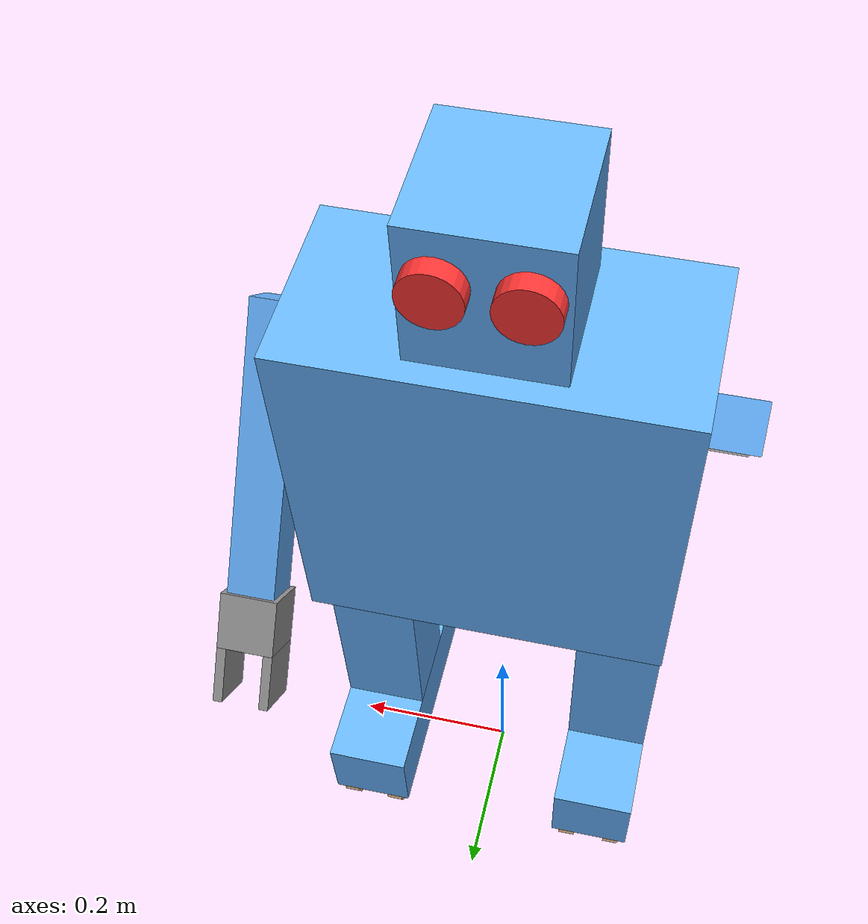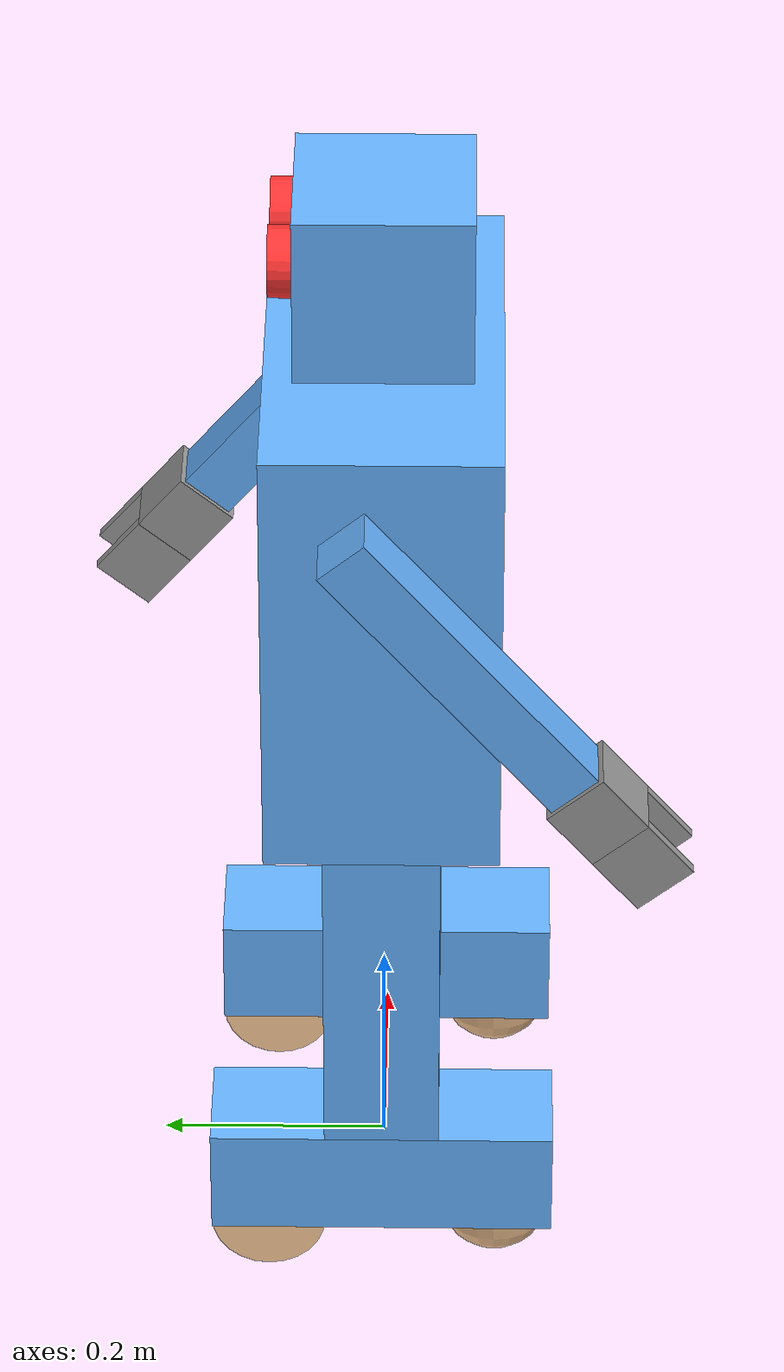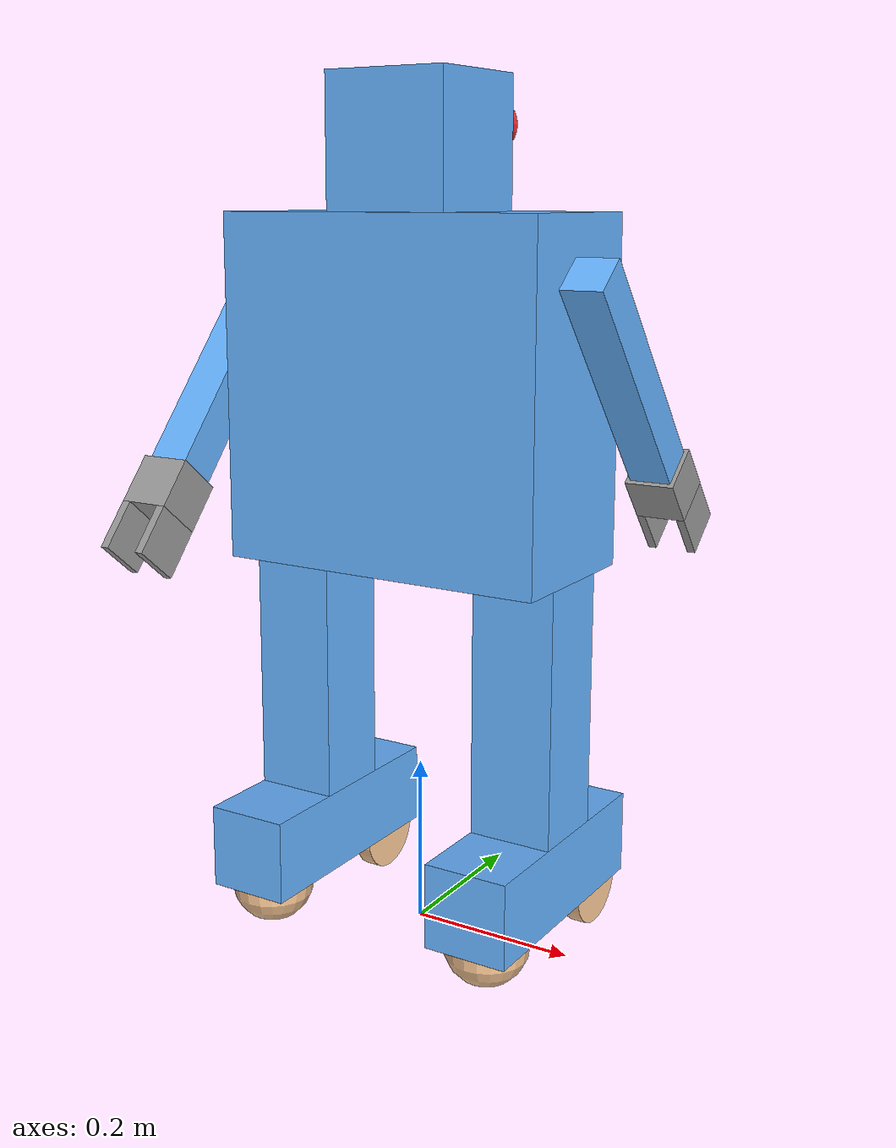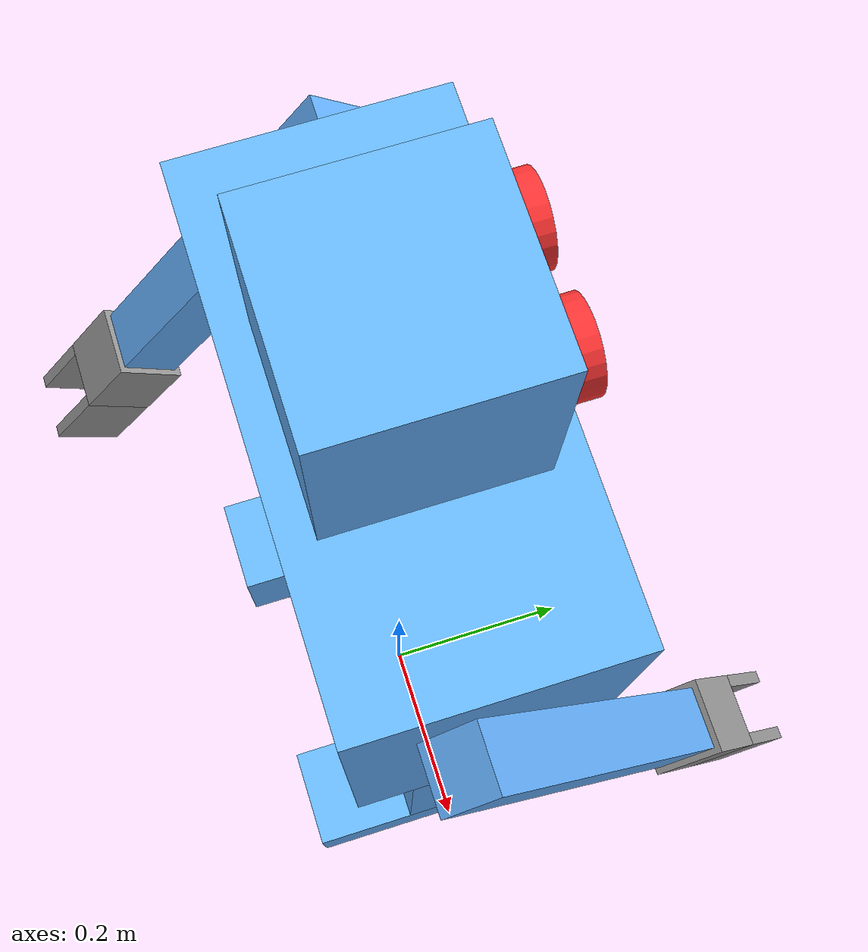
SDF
<?xml version='1.0'?>
<sdf version='1.6'>
  <model name='Vintage_Robot'>
    <link name='link_0_clone'>
      <pose frame=''>0.15 -0 0.1 0 -0 0</pose>
      <inertial>
        <mass>1</mass>
        <inertia>
          <ixx>0.166667</ixx>
          <ixy>0</ixy>
          <ixz>0</ixz>
          <iyy>0.166667</iyy>
          <iyz>0</iyz>
          <izz>0.166667</izz>
        </inertia>
        <pose frame=''>0 0 0 0 -0 0</pose>
      </inertial>
      <self_collide>0</self_collide>
      <kinematic>0</kinematic>
      <visual name='visual'>
        <pose frame=''>0 0 0 0 -0 0</pose>
        <geometry>
          <box>
            <size>0.1 0.3 0.1</size>
          </box>
        </geometry>
        <material>
          <lighting>1</lighting>
          <script>
            <uri>file://media/materials/scripts/gazebo.material</uri>
            <name>Gazebo/Grey</name>
          </script>
          <shader type='pixel'>
            <normal_map>__default__</normal_map>
          </shader>
          <ambient>0.4 0.7 1 1</ambient>
          <diffuse>0.7 0.7 0.7 1</diffuse>
          <specular>0.01 0.01 0.01 1</specular>
          <emissive>0 0 0 1</emissive>
        </material>
        <transparency>0</transparency>
        <cast_shadows>1</cast_shadows>
      </visual>
      <collision name='collision'>
        <laser_retro>0</laser_retro>
        <max_contacts>10</max_contacts>
        <pose frame=''>0 0 0 0 -0 0</pose>
        <geometry>
          <box>
            <size>0.1 0.3 0.1</size>
          </box>
        </geometry>
        <surface>
          <friction>
            <ode>
              <mu>1</mu>
              <mu2>1</mu2>
              <fdir1>0 0 0</fdir1>
              <slip1>0</slip1>
              <slip2>0</slip2>
            </ode>
            <torsional>
              <coefficient>1</coefficient>
              <patch_radius>0</patch_radius>
              <surface_radius>0</surface_radius>
              <use_patch_radius>1</use_patch_radius>
              <ode>
                <slip>0</slip>
              </ode>
            </torsional>
          </friction>
          <bounce>
            <restitution_coefficient>0</restitution_coefficient>
            <threshold>1e+06</threshold>
          </bounce>
          <contact>
            <collide_without_contact>0</collide_without_contact>
            <collide_without_contact_bitmask>1</collide_without_contact_bitmask>
            <collide_bitmask>1</collide_bitmask>
            <ode>
              <soft_cfm>0</soft_cfm>
              <soft_erp>0.2</soft_erp>
              <kp>1e+13</kp>
              <kd>1</kd>
              <max_vel>0.01</max_vel>
              <min_depth>0</min_depth>
            </ode>
            <bullet>
              <split_impulse>1</split_impulse>
              <split_impulse_penetration_threshold>-0.01</split_impulse_penetration_threshold>
              <soft_cfm>0</soft_cfm>
              <soft_erp>0.2</soft_erp>
              <kp>1e+13</kp>
              <kd>1</kd>
            </bullet>
          </contact>
        </surface>
      </collision>
    </link>
    <link name='link_0'>
      <pose frame=''>0.225 0 0.75 0.7 -0 0</pose>
      <inertial>
        <mass>1</mass>
        <inertia>
          <ixx>0.166667</ixx>
          <ixy>0</ixy>
          <ixz>0</ixz>
          <iyy>0.166667</iyy>
          <iyz>0</iyz>
          <izz>0.166667</izz>
        </inertia>
        <pose frame=''>0 0 0 0 -0 0</pose>
      </inertial>
      <self_collide>0</self_collide>
      <kinematic>0</kinematic>
      <visual name='visual'>
        <pose frame=''>0 0 -0.1 0 -0 0</pose>
        <geometry>
          <box>
            <size>0.05 0.05 0.3</size>
          </box>
        </geometry>
        <material>
          <lighting>1</lighting>
          <script>
            <uri>file://media/materials/scripts/gazebo.material</uri>
            <name>Gazebo/Grey</name>
          </script>
          <shader type='pixel'>
            <normal_map>__default__</normal_map>
          </shader>
          <ambient>0.4 0.7 1 1</ambient>
          <diffuse>0.7 0.7 0.7 1</diffuse>
          <specular>0.01 0.01 0.01 1</specular>
          <emissive>0 0 0 1</emissive>
        </material>
        <transparency>0</transparency>
        <cast_shadows>1</cast_shadows>
      </visual>
      <collision name='collision'>
        <laser_retro>0</laser_retro>
        <max_contacts>10</max_contacts>
        <pose frame=''>0 0 -0.1 0 -0 0</pose>
        <geometry>
          <box>
            <size>0.05 0.05 0.3</size>
          </box>
        </geometry>
        <surface>
          <friction>
            <ode>
              <mu>1</mu>
              <mu2>1</mu2>
              <fdir1>0 0 0</fdir1>
              <slip1>0</slip1>
              <slip2>0</slip2>
            </ode>
            <torsional>
              <coefficient>1</coefficient>
              <patch_radius>0</patch_radius>
              <surface_radius>0</surface_radius>
              <use_patch_radius>1</use_patch_radius>
              <ode>
                <slip>0</slip>
              </ode>
            </torsional>
          </friction>
          <bounce>
            <restitution_coefficient>0</restitution_coefficient>
            <threshold>1e+06</threshold>
          </bounce>
          <contact>
            <collide_without_contact>0</collide_without_contact>
            <collide_without_contact_bitmask>1</collide_without_contact_bitmask>
            <collide_bitmask>1</collide_bitmask>
            <ode>
              <soft_cfm>0</soft_cfm>
              <soft_erp>0.2</soft_erp>
              <kp>1e+13</kp>
              <kd>1</kd>
              <max_vel>0.01</max_vel>
              <min_depth>0</min_depth>
            </ode>
            <bullet>
              <split_impulse>1</split_impulse>
              <split_impulse_penetration_threshold>-0.01</split_impulse_penetration_threshold>
              <soft_cfm>0</soft_cfm>
              <soft_erp>0.2</soft_erp>
              <kp>1e+13</kp>
              <kd>1</kd>
            </bullet>
          </contact>
        </surface>
      </collision>
    </link>
    <link name='link_0_0'>
      <pose frame=''>0.04 0.08 0.945 1.5707 0 -3.14159</pose>
      <inertial>
        <mass>1</mass>
        <inertia>
          <ixx>0.145833</ixx>
          <ixy>0</ixy>
          <ixz>0</ixz>
          <iyy>0.145833</iyy>
          <iyz>0</iyz>
          <izz>0.125</izz>
        </inertia>
        <pose frame=''>0 0 0 0 -0 0</pose>
      </inertial>
      <self_collide>0</self_collide>
      <kinematic>0</kinematic>
      <visual name='visual'>
        <pose frame=''>0 0 0 0 -0 0</pose>
        <geometry>
          <cylinder>
            <radius>0.03</radius>
            <length>0.03</length>
          </cylinder>
        </geometry>
        <material>
          <lighting>1</lighting>
          <script>
            <uri>file://media/materials/scripts/gazebo.material</uri>
            <name>Gazebo/Grey</name>
          </script>
          <shader type='pixel'>
            <normal_map>__default__</normal_map>
          </shader>
          <ambient>1 0.2 0.2 1</ambient>
          <diffuse>0.7 0.7 0.7 1</diffuse>
          <specular>0.01 0.01 0.01 1</specular>
          <emissive>0 0 0 1</emissive>
        </material>
        <transparency>0</transparency>
        <cast_shadows>1</cast_shadows>
      </visual>
      <collision name='collision'>
        <laser_retro>0</laser_retro>
        <max_contacts>10</max_contacts>
        <pose frame=''>0 0 0 0 -0 0</pose>
        <geometry>
          <cylinder>
            <radius>0.03</radius>
            <length>0.03</length>
          </cylinder>
        </geometry>
        <surface>
          <friction>
            <ode>
              <mu>1</mu>
              <mu2>1</mu2>
              <fdir1>0 0 0</fdir1>
              <slip1>0</slip1>
              <slip2>0</slip2>
            </ode>
            <torsional>
              <coefficient>1</coefficient>
              <patch_radius>0</patch_radius>
              <surface_radius>0</surface_radius>
              <use_patch_radius>1</use_patch_radius>
              <ode>
                <slip>0</slip>
              </ode>
            </torsional>
          </friction>
          <bounce>
            <restitution_coefficient>0</restitution_coefficient>
            <threshold>1e+06</threshold>
          </bounce>
          <contact>
            <collide_without_contact>0</collide_without_contact>
            <collide_without_contact_bitmask>1</collide_without_contact_bitmask>
            <collide_bitmask>1</collide_bitmask>
            <ode>
              <soft_cfm>0</soft_cfm>
              <soft_erp>0.2</soft_erp>
              <kp>1e+13</kp>
              <kd>1</kd>
              <max_vel>0.01</max_vel>
              <min_depth>0</min_depth>
            </ode>
            <bullet>
              <split_impulse>1</split_impulse>
              <split_impulse_penetration_threshold>-0.01</split_impulse_penetration_threshold>
              <soft_cfm>0</soft_cfm>
              <soft_erp>0.2</soft_erp>
              <kp>1e+13</kp>
              <kd>1</kd>
            </bullet>
          </contact>
        </surface>
      </collision>
    </link>
    <link name='link_0_0_clone'>
      <pose frame=''>-0.04 0.08 0.945 1.5707 -0 5e-06</pose>
      <inertial>
        <mass>1</mass>
        <inertia>
          <ixx>0.145833</ixx>
          <ixy>0</ixy>
          <ixz>0</ixz>
          <iyy>0.145833</iyy>
          <iyz>0</iyz>
          <izz>0.125</izz>
        </inertia>
        <pose frame=''>0 0 0 0 -0 0</pose>
      </inertial>
      <self_collide>0</self_collide>
      <kinematic>0</kinematic>
      <visual name='visual_0'>
        <pose frame=''>0 0 0 0 -0 0</pose>
        <geometry>
          <cylinder>
            <radius>0.03</radius>
            <length>0.03</length>
          </cylinder>
        </geometry>
        <material>
          <lighting>1</lighting>
          <script>
            <uri>file://media/materials/scripts/gazebo.material</uri>
            <name>Gazebo/Grey</name>
          </script>
          <shader type='pixel'>
            <normal_map>__default__</normal_map>
          </shader>
          <ambient>1 0.2 0.2 1</ambient>
          <diffuse>0.7 0.7 0.7 1</diffuse>
          <specular>0.01 0.01 0.01 1</specular>
          <emissive>0 0 0 1</emissive>
        </material>
        <transparency>0</transparency>
        <cast_shadows>1</cast_shadows>
      </visual>
      <collision name='collision'>
        <laser_retro>0</laser_retro>
        <max_contacts>10</max_contacts>
        <pose frame=''>0 0 0 0 -0 0</pose>
        <geometry>
          <cylinder>
            <radius>0.03</radius>
            <length>0.03</length>
          </cylinder>
        </geometry>
        <surface>
          <friction>
            <ode>
              <mu>1</mu>
              <mu2>1</mu2>
              <fdir1>0 0 0</fdir1>
              <slip1>0</slip1>
              <slip2>0</slip2>
            </ode>
            <torsional>
              <coefficient>1</coefficient>
              <patch_radius>0</patch_radius>
              <surface_radius>0</surface_radius>
              <use_patch_radius>1</use_patch_radius>
              <ode>
                <slip>0</slip>
              </ode>
            </torsional>
          </friction>
          <bounce>
            <restitution_coefficient>0</restitution_coefficient>
            <threshold>1e+06</threshold>
          </bounce>
          <contact>
            <collide_without_contact>0</collide_without_contact>
            <collide_without_contact_bitmask>1</collide_without_contact_bitmask>
            <collide_bitmask>1</collide_bitmask>
            <ode>
              <soft_cfm>0</soft_cfm>
              <soft_erp>0.2</soft_erp>
              <kp>1e+13</kp>
              <kd>1</kd>
              <max_vel>0.01</max_vel>
              <min_depth>0</min_depth>
            </ode>
            <bullet>
              <split_impulse>1</split_impulse>
              <split_impulse_penetration_threshold>-0.01</split_impulse_penetration_threshold>
              <soft_cfm>0</soft_cfm>
              <soft_erp>0.2</soft_erp>
              <kp>1e+13</kp>
              <kd>1</kd>
            </bullet>
          </contact>
        </surface>
      </collision>
    </link>
    <link name='link_0_1'>
      <pose frame=''>-0 0 0.925 0 -0 0</pose>
      <inertial>
        <mass>1</mass>
        <inertia>
          <ixx>0.166667</ixx>
          <ixy>0</ixy>
          <ixz>0</ixz>
          <iyy>0.166667</iyy>
          <iyz>0</iyz>
          <izz>0.166667</izz>
        </inertia>
        <pose frame=''>0 0 0 0 -0 0</pose>
      </inertial>
      <self_collide>0</self_collide>
      <kinematic>0</kinematic>
      <visual name='visual'>
        <pose frame=''>0 0 0 0 -0 0</pose>
        <geometry>
          <box>
            <size>0.15 0.15 0.15</size>
          </box>
        </geometry>
        <material>
          <lighting>1</lighting>
          <script>
            <uri>file://media/materials/scripts/gazebo.material</uri>
            <name>Gazebo/Grey</name>
          </script>
          <shader type='pixel'>
            <normal_map>__default__</normal_map>
          </shader>
          <ambient>0.4 0.7 1 1</ambient>
          <diffuse>0.7 0.7 0.7 1</diffuse>
          <specular>0.01 0.01 0.01 1</specular>
          <emissive>0 0 0 1</emissive>
        </material>
        <transparency>0</transparency>
        <cast_shadows>1</cast_shadows>
      </visual>
      <collision name='collision'>
        <laser_retro>0</laser_retro>
        <max_contacts>10</max_contacts>
        <pose frame=''>0 0 0 0 -0 0</pose>
        <geometry>
          <box>
            <size>0.15 0.15 0.15</size>
          </box>
        </geometry>
        <surface>
          <friction>
            <ode>
              <mu>1</mu>
              <mu2>1</mu2>
              <fdir1>0 0 0</fdir1>
              <slip1>0</slip1>
              <slip2>0</slip2>
            </ode>
            <torsional>
              <coefficient>1</coefficient>
              <patch_radius>0</patch_radius>
              <surface_radius>0</surface_radius>
              <use_patch_radius>1</use_patch_radius>
              <ode>
                <slip>0</slip>
              </ode>
            </torsional>
          </friction>
          <bounce>
            <restitution_coefficient>0</restitution_coefficient>
            <threshold>1e+06</threshold>
          </bounce>
          <contact>
            <collide_without_contact>0</collide_without_contact>
            <collide_without_contact_bitmask>1</collide_without_contact_bitmask>
            <collide_bitmask>1</collide_bitmask>
            <ode>
              <soft_cfm>0</soft_cfm>
              <soft_erp>0.2</soft_erp>
              <kp>1e+13</kp>
              <kd>1</kd>
              <max_vel>0.01</max_vel>
              <min_depth>0</min_depth>
            </ode>
            <bullet>
              <split_impulse>1</split_impulse>
              <split_impulse_penetration_threshold>-0.01</split_impulse_penetration_threshold>
              <soft_cfm>0</soft_cfm>
              <soft_erp>0.2</soft_erp>
              <kp>1e+13</kp>
              <kd>1</kd>
            </bullet>
          </contact>
        </surface>
      </collision>
    </link>
    <link name='link_0_clone_0'>
      <pose frame=''>-0.15 -0 0.1 0 -0 0</pose>
      <inertial>
        <mass>1</mass>
        <inertia>
          <ixx>0.166667</ixx>
          <ixy>0</ixy>
          <ixz>0</ixz>
          <iyy>0.166667</iyy>
          <iyz>0</iyz>
          <izz>0.166667</izz>
        </inertia>
        <pose frame=''>0 0 0 0 -0 0</pose>
      </inertial>
      <self_collide>0</self_collide>
      <kinematic>0</kinematic>
      <visual name='visual'>
        <pose frame=''>0 0 0 0 -0 0</pose>
        <geometry>
          <box>
            <size>0.1 0.3 0.1</size>
          </box>
        </geometry>
        <material>
          <lighting>1</lighting>
          <script>
            <uri>file://media/materials/scripts/gazebo.material</uri>
            <name>Gazebo/Grey</name>
          </script>
          <shader type='pixel'>
            <normal_map>__default__</normal_map>
          </shader>
          <ambient>0.4 0.7 1 1</ambient>
          <diffuse>0.7 0.7 0.7 1</diffuse>
          <specular>0.01 0.01 0.01 1</specular>
          <emissive>0 0 0 1</emissive>
        </material>
        <transparency>0</transparency>
        <cast_shadows>1</cast_shadows>
      </visual>
      <collision name='collision'>
        <laser_retro>0</laser_retro>
        <max_contacts>10</max_contacts>
        <pose frame=''>0 0 0 0 -0 0</pose>
        <geometry>
          <box>
            <size>0.1 0.3 0.1</size>
          </box>
        </geometry>
        <surface>
          <friction>
            <ode>
              <mu>1</mu>
              <mu2>1</mu2>
              <fdir1>0 0 0</fdir1>
              <slip1>0</slip1>
              <slip2>0</slip2>
            </ode>
            <torsional>
              <coefficient>1</coefficient>
              <patch_radius>0</patch_radius>
              <surface_radius>0</surface_radius>
              <use_patch_radius>1</use_patch_radius>
              <ode>
                <slip>0</slip>
              </ode>
            </torsional>
          </friction>
          <bounce>
            <restitution_coefficient>0</restitution_coefficient>
            <threshold>1e+06</threshold>
          </bounce>
          <contact>
            <collide_without_contact>0</collide_without_contact>
            <collide_without_contact_bitmask>1</collide_without_contact_bitmask>
            <collide_bitmask>1</collide_bitmask>
            <ode>
              <soft_cfm>0</soft_cfm>
              <soft_erp>0.2</soft_erp>
              <kp>1e+13</kp>
              <kd>1</kd>
              <max_vel>0.01</max_vel>
              <min_depth>0</min_depth>
            </ode>
            <bullet>
              <split_impulse>1</split_impulse>
              <split_impulse_penetration_threshold>-0.01</split_impulse_penetration_threshold>
              <soft_cfm>0</soft_cfm>
              <soft_erp>0.2</soft_erp>
              <kp>1e+13</kp>
              <kd>1</kd>
            </bullet>
          </contact>
        </surface>
      </collision>
    </link>
    <link name='link_0_clone_1'>
      <pose frame=''>-0.225 0 0.75 -0.7 -0 -0</pose>
      <inertial>
        <mass>1</mass>
        <inertia>
          <ixx>0.166667</ixx>
          <ixy>0</ixy>
          <ixz>0</ixz>
          <iyy>0.166667</iyy>
          <iyz>0</iyz>
          <izz>0.166667</izz>
        </inertia>
        <pose frame=''>0 0 0 0 -0 0</pose>
      </inertial>
      <self_collide>0</self_collide>
      <kinematic>0</kinematic>
      <visual name='visual'>
        <pose frame=''>0 0 -0.1 0 -0 0</pose>
        <geometry>
          <box>
            <size>0.05 0.05 0.3</size>
          </box>
        </geometry>
        <material>
          <lighting>1</lighting>
          <script>
            <uri>file://media/materials/scripts/gazebo.material</uri>
            <name>Gazebo/Grey</name>
          </script>
          <shader type='pixel'>
            <normal_map>__default__</normal_map>
          </shader>
          <ambient>0.4 0.7 1 1</ambient>
          <diffuse>0.7 0.7 0.7 1</diffuse>
          <specular>0.01 0.01 0.01 1</specular>
          <emissive>0 0 0 1</emissive>
        </material>
        <transparency>0</transparency>
        <cast_shadows>1</cast_shadows>
      </visual>
      <collision name='collision'>
        <laser_retro>0</laser_retro>
        <max_contacts>10</max_contacts>
        <pose frame=''>0 0 -0.1 0 -0 0</pose>
        <geometry>
          <box>
            <size>0.05 0.05 0.3</size>
          </box>
        </geometry>
        <surface>
          <friction>
            <ode>
              <mu>1</mu>
              <mu2>1</mu2>
              <fdir1>0 0 0</fdir1>
              <slip1>0</slip1>
              <slip2>0</slip2>
            </ode>
            <torsional>
              <coefficient>1</coefficient>
              <patch_radius>0</patch_radius>
              <surface_radius>0</surface_radius>
              <use_patch_radius>1</use_patch_radius>
              <ode>
                <slip>0</slip>
              </ode>
            </torsional>
          </friction>
          <bounce>
            <restitution_coefficient>0</restitution_coefficient>
            <threshold>1e+06</threshold>
          </bounce>
          <contact>
            <collide_without_contact>0</collide_without_contact>
            <collide_without_contact_bitmask>1</collide_without_contact_bitmask>
            <collide_bitmask>1</collide_bitmask>
            <ode>
              <soft_cfm>0</soft_cfm>
              <soft_erp>0.2</soft_erp>
              <kp>1e+13</kp>
              <kd>1</kd>
              <max_vel>0.01</max_vel>
              <min_depth>0</min_depth>
            </ode>
            <bullet>
              <split_impulse>1</split_impulse>
              <split_impulse_penetration_threshold>-0.01</split_impulse_penetration_threshold>
              <soft_cfm>0</soft_cfm>
              <soft_erp>0.2</soft_erp>
              <kp>1e+13</kp>
              <kd>1</kd>
            </bullet>
          </contact>
        </surface>
      </collision>
    </link>
    <link name='link_1'>
      <pose frame=''>0.25 0.219034 0.489954 0.7 -0 0</pose>
      <inertial>
        <mass>1</mass>
        <inertia>
          <ixx>0.166667</ixx>
          <ixy>0</ixy>
          <ixz>0</ixz>
          <iyy>0.166667</iyy>
          <iyz>0</iyz>
          <izz>0.166667</izz>
        </inertia>
        <pose frame=''>0 0 0 0 -0 0</pose>
      </inertial>
      <self_collide>0</self_collide>
      <kinematic>0</kinematic>
      <visual name='visual'>
        <pose frame=''>0 0 0 0 -0 0</pose>
        <geometry>
          <box>
            <size>0.01 0.06 0.06</size>
          </box>
        </geometry>
        <material>
          <lighting>1</lighting>
          <script>
            <uri>file://media/materials/scripts/gazebo.material</uri>
            <name>Gazebo/Grey</name>
          </script>
          <shader type='pixel'>
            <normal_map>__default__</normal_map>
          </shader>
          <ambient>0.75 0.75 0.75 1</ambient>
          <diffuse>0.7 0.7 0.7 1</diffuse>
          <specular>0.01 0.01 0.01 1</specular>
          <emissive>0 0 0 1</emissive>
        </material>
        <transparency>0</transparency>
        <cast_shadows>1</cast_shadows>
      </visual>
      <collision name='collision'>
        <laser_retro>0</laser_retro>
        <max_contacts>10</max_contacts>
        <pose frame=''>0 0 0 0 -0 0</pose>
        <geometry>
          <box>
            <size>0.01 0.06 0.06</size>
          </box>
        </geometry>
        <surface>
          <friction>
            <ode>
              <mu>1</mu>
              <mu2>1</mu2>
              <fdir1>0 0 0</fdir1>
              <slip1>0</slip1>
              <slip2>0</slip2>
            </ode>
            <torsional>
              <coefficient>1</coefficient>
              <patch_radius>0</patch_radius>
              <surface_radius>0</surface_radius>
              <use_patch_radius>1</use_patch_radius>
              <ode>
                <slip>0</slip>
              </ode>
            </torsional>
          </friction>
          <bounce>
            <restitution_coefficient>0</restitution_coefficient>
            <threshold>1e+06</threshold>
          </bounce>
          <contact>
            <collide_without_contact>0</collide_without_contact>
            <collide_without_contact_bitmask>1</collide_without_contact_bitmask>
            <collide_bitmask>1</collide_bitmask>
            <ode>
              <soft_cfm>0</soft_cfm>
              <soft_erp>0.2</soft_erp>
              <kp>1e+13</kp>
              <kd>1</kd>
              <max_vel>0.01</max_vel>
              <min_depth>0</min_depth>
            </ode>
            <bullet>
              <split_impulse>1</split_impulse>
              <split_impulse_penetration_threshold>-0.01</split_impulse_penetration_threshold>
              <soft_cfm>0</soft_cfm>
              <soft_erp>0.2</soft_erp>
              <kp>1e+13</kp>
              <kd>1</kd>
            </bullet>
          </contact>
        </surface>
      </collision>
    </link>
    <link name='link_1_clone'>
      <pose frame=''>0.120005 0.1 0.05 0.001508 1.5707 0.001508</pose>
      <inertial>
        <mass>1</mass>
        <inertia>
          <ixx>0.145833</ixx>
          <ixy>0</ixy>
          <ixz>0</ixz>
          <iyy>0.145833</iyy>
          <iyz>0</iyz>
          <izz>0.125</izz>
        </inertia>
        <pose frame=''>0 0 0 0 -0 0</pose>
      </inertial>
      <self_collide>0</self_collide>
      <kinematic>0</kinematic>
      <visual name='visual'>
        <pose frame=''>0 0 0 0 -0 0</pose>
        <geometry>
          <cylinder>
            <radius>0.05</radius>
            <length>0.02</length>
          </cylinder>
        </geometry>
        <material>
          <lighting>1</lighting>
          <script>
            <uri>file://media/materials/scripts/gazebo.material</uri>
            <name>Gazebo/Grey</name>
          </script>
          <shader type='pixel'>
            <normal_map>__default__</normal_map>
          </shader>
          <ambient>1 0.8 0.6 1</ambient>
          <diffuse>0.7 0.7 0.7 1</diffuse>
          <specular>0.01 0.01 0.01 1</specular>
          <emissive>0 0 0 1</emissive>
        </material>
        <transparency>0</transparency>
        <cast_shadows>1</cast_shadows>
      </visual>
      <collision name='collision'>
        <laser_retro>0</laser_retro>
        <max_contacts>10</max_contacts>
        <pose frame=''>0 0 0 0 -0 0</pose>
        <geometry>
          <cylinder>
            <radius>0.05</radius>
            <length>0.02</length>
          </cylinder>
        </geometry>
        <surface>
          <friction>
            <ode>
              <mu>1</mu>
              <mu2>1</mu2>
              <fdir1>0 0 0</fdir1>
              <slip1>0</slip1>
              <slip2>0</slip2>
            </ode>
            <torsional>
              <coefficient>1</coefficient>
              <patch_radius>0</patch_radius>
              <surface_radius>0</surface_radius>
              <use_patch_radius>1</use_patch_radius>
              <ode>
                <slip>0</slip>
              </ode>
            </torsional>
          </friction>
          <bounce>
            <restitution_coefficient>0</restitution_coefficient>
            <threshold>1e+06</threshold>
          </bounce>
          <contact>
            <collide_without_contact>0</collide_without_contact>
            <collide_without_contact_bitmask>1</collide_without_contact_bitmask>
            <collide_bitmask>1</collide_bitmask>
            <ode>
              <soft_cfm>0</soft_cfm>
              <soft_erp>0.2</soft_erp>
              <kp>1e+13</kp>
              <kd>1</kd>
              <max_vel>0.01</max_vel>
              <min_depth>0</min_depth>
            </ode>
            <bullet>
              <split_impulse>1</split_impulse>
              <split_impulse_penetration_threshold>-0.01</split_impulse_penetration_threshold>
              <soft_cfm>0</soft_cfm>
              <soft_erp>0.2</soft_erp>
              <kp>1e+13</kp>
              <kd>1</kd>
            </bullet>
          </contact>
        </surface>
      </collision>
    </link>
    <link name='link_1_clone_0'>
      <pose frame=''>-0.179995 0.1 0.05 0.000879 1.5707 0.000879</pose>
      <inertial>
        <mass>1</mass>
        <inertia>
          <ixx>0.145833</ixx>
          <ixy>0</ixy>
          <ixz>0</ixz>
          <iyy>0.145833</iyy>
          <iyz>0</iyz>
          <izz>0.125</izz>
        </inertia>
        <pose frame=''>0 0 0 0 -0 0</pose>
      </inertial>
      <self_collide>0</self_collide>
      <kinematic>0</kinematic>
      <gravity>1</gravity>
      <visual name='visual'>
        <pose frame=''>0 0 0 0 -0 0</pose>
        <geometry>
          <cylinder>
            <radius>0.05</radius>
            <length>0.02</length>
          </cylinder>
        </geometry>
        <material>
          <lighting>1</lighting>
          <script>
            <uri>file://media/materials/scripts/gazebo.material</uri>
            <name>Gazebo/Grey</name>
          </script>
          <shader type='pixel'>
            <normal_map>__default__</normal_map>
          </shader>
          <ambient>1 0.8 0.6 1</ambient>
          <diffuse>0.7 0.7 0.7 1</diffuse>
          <specular>0.01 0.01 0.01 1</specular>
          <emissive>0 0 0 1</emissive>
        </material>
        <transparency>0</transparency>
        <cast_shadows>1</cast_shadows>
      </visual>
      <collision name='collision'>
        <laser_retro>0</laser_retro>
        <max_contacts>10</max_contacts>
        <pose frame=''>0 0 0 0 -0 0</pose>
        <geometry>
          <cylinder>
            <radius>0.05</radius>
            <length>0.02</length>
          </cylinder>
        </geometry>
        <surface>
          <friction>
            <ode>
              <mu>1</mu>
              <mu2>1</mu2>
              <fdir1>0 0 0</fdir1>
              <slip1>0</slip1>
              <slip2>0</slip2>
            </ode>
            <torsional>
              <coefficient>1</coefficient>
              <patch_radius>0</patch_radius>
              <surface_radius>0</surface_radius>
              <use_patch_radius>1</use_patch_radius>
              <ode>
                <slip>0</slip>
              </ode>
            </torsional>
          </friction>
          <bounce>
            <restitution_coefficient>0</restitution_coefficient>
            <threshold>1e+06</threshold>
          </bounce>
          <contact>
            <collide_without_contact>0</collide_without_contact>
            <collide_without_contact_bitmask>1</collide_without_contact_bitmask>
            <collide_bitmask>1</collide_bitmask>
            <ode>
              <soft_cfm>0</soft_cfm>
              <soft_erp>0.2</soft_erp>
              <kp>1e+13</kp>
              <kd>1</kd>
              <max_vel>0.01</max_vel>
              <min_depth>0</min_depth>
            </ode>
            <bullet>
              <split_impulse>1</split_impulse>
              <split_impulse_penetration_threshold>-0.01</split_impulse_penetration_threshold>
              <soft_cfm>0</soft_cfm>
              <soft_erp>0.2</soft_erp>
              <kp>1e+13</kp>
              <kd>1</kd>
            </bullet>
          </contact>
        </surface>
      </collision>
    </link>
    <link name='link_1_clone_0_clone'>
      <pose frame=''>-0.120005 0.1 0.05 0.000879 1.5707 0.000879</pose>
      <inertial>
        <mass>1</mass>
        <inertia>
          <ixx>0.145833</ixx>
          <ixy>0</ixy>
          <ixz>0</ixz>
          <iyy>0.145833</iyy>
          <iyz>0</iyz>
          <izz>0.125</izz>
        </inertia>
        <pose frame=''>0 0 0 0 -0 0</pose>
      </inertial>
      <self_collide>0</self_collide>
      <kinematic>0</kinematic>
      <visual name='visual'>
        <pose frame=''>0 0 0 0 -0 0</pose>
        <geometry>
          <cylinder>
            <radius>0.05</radius>
            <length>0.02</length>
          </cylinder>
        </geometry>
        <material>
          <lighting>1</lighting>
          <script>
            <uri>file://media/materials/scripts/gazebo.material</uri>
            <name>Gazebo/Grey</name>
          </script>
          <shader type='pixel'>
            <normal_map>__default__</normal_map>
          </shader>
          <ambient>1 0.8 0.6 1</ambient>
          <diffuse>0.7 0.7 0.7 1</diffuse>
          <specular>0.01 0.01 0.01 1</specular>
          <emissive>0 0 0 1</emissive>
        </material>
        <transparency>0</transparency>
        <cast_shadows>1</cast_shadows>
      </visual>
      <collision name='collision'>
        <laser_retro>0</laser_retro>
        <max_contacts>10</max_contacts>
        <pose frame=''>0 0 0 0 -0 0</pose>
        <geometry>
          <cylinder>
            <radius>0.05</radius>
            <length>0.02</length>
          </cylinder>
        </geometry>
        <surface>
          <friction>
            <ode>
              <mu>1</mu>
              <mu2>1</mu2>
              <fdir1>0 0 0</fdir1>
              <slip1>0</slip1>
              <slip2>0</slip2>
            </ode>
            <torsional>
              <coefficient>1</coefficient>
              <patch_radius>0</patch_radius>
              <surface_radius>0</surface_radius>
              <use_patch_radius>1</use_patch_radius>
              <ode>
                <slip>0</slip>
              </ode>
            </torsional>
          </friction>
          <bounce>
            <restitution_coefficient>0</restitution_coefficient>
            <threshold>1e+06</threshold>
          </bounce>
          <contact>
            <collide_without_contact>0</collide_without_contact>
            <collide_without_contact_bitmask>1</collide_without_contact_bitmask>
            <collide_bitmask>1</collide_bitmask>
            <ode>
              <soft_cfm>0</soft_cfm>
              <soft_erp>0.2</soft_erp>
              <kp>1e+13</kp>
              <kd>1</kd>
              <max_vel>0.01</max_vel>
              <min_depth>0</min_depth>
            </ode>
            <bullet>
              <split_impulse>1</split_impulse>
              <split_impulse_penetration_threshold>-0.01</split_impulse_penetration_threshold>
              <soft_cfm>0</soft_cfm>
              <soft_erp>0.2</soft_erp>
              <kp>1e+13</kp>
              <kd>1</kd>
            </bullet>
          </contact>
        </surface>
      </collision>
    </link>
    <link name='link_1_clone_1'>
      <pose frame=''>0.2 0.219034 0.489954 0.7 -0 0</pose>
      <inertial>
        <mass>1</mass>
        <inertia>
          <ixx>0.166667</ixx>
          <ixy>0</ixy>
          <ixz>0</ixz>
          <iyy>0.166667</iyy>
          <iyz>0</iyz>
          <izz>0.166667</izz>
        </inertia>
        <pose frame=''>0 0 0 0 -0 0</pose>
      </inertial>
      <self_collide>0</self_collide>
      <kinematic>0</kinematic>
      <visual name='visual'>
        <pose frame=''>0 0 0 0 -0 0</pose>
        <geometry>
          <box>
            <size>0.01 0.06 0.06</size>
          </box>
        </geometry>
        <material>
          <lighting>1</lighting>
          <script>
            <uri>file://media/materials/scripts/gazebo.material</uri>
            <name>Gazebo/Grey</name>
          </script>
          <shader type='pixel'>
            <normal_map>__default__</normal_map>
          </shader>
          <ambient>0.75 0.75 0.75 1</ambient>
          <diffuse>0.7 0.7 0.7 1</diffuse>
          <specular>0.01 0.01 0.01 1</specular>
          <emissive>0 0 0 1</emissive>
        </material>
        <transparency>0</transparency>
        <cast_shadows>1</cast_shadows>
      </visual>
      <collision name='collision'>
        <laser_retro>0</laser_retro>
        <max_contacts>10</max_contacts>
        <pose frame=''>0 0 0 0 -0 0</pose>
        <geometry>
          <box>
            <size>0.01 0.06 0.06</size>
          </box>
        </geometry>
        <surface>
          <friction>
            <ode>
              <mu>1</mu>
              <mu2>1</mu2>
              <fdir1>0 0 0</fdir1>
              <slip1>0</slip1>
              <slip2>0</slip2>
            </ode>
            <torsional>
              <coefficient>1</coefficient>
              <patch_radius>0</patch_radius>
              <surface_radius>0</surface_radius>
              <use_patch_radius>1</use_patch_radius>
              <ode>
                <slip>0</slip>
              </ode>
            </torsional>
          </friction>
          <bounce>
            <restitution_coefficient>0</restitution_coefficient>
            <threshold>1e+06</threshold>
          </bounce>
          <contact>
            <collide_without_contact>0</collide_without_contact>
            <collide_without_contact_bitmask>1</collide_without_contact_bitmask>
            <collide_bitmask>1</collide_bitmask>
            <ode>
              <soft_cfm>0</soft_cfm>
              <soft_erp>0.2</soft_erp>
              <kp>1e+13</kp>
              <kd>1</kd>
              <max_vel>0.01</max_vel>
              <min_depth>0</min_depth>
            </ode>
            <bullet>
              <split_impulse>1</split_impulse>
              <split_impulse_penetration_threshold>-0.01</split_impulse_penetration_threshold>
              <soft_cfm>0</soft_cfm>
              <soft_erp>0.2</soft_erp>
              <kp>1e+13</kp>
              <kd>1</kd>
            </bullet>
          </contact>
        </surface>
      </collision>
    </link>
    <link name='link_1_clone_1_clone'>
      <pose frame=''>-0.2 -0.219034 0.489954 -0.7 -0 -0</pose>
      <inertial>
        <mass>1</mass>
        <inertia>
          <ixx>0.166667</ixx>
          <ixy>0</ixy>
          <ixz>0</ixz>
          <iyy>0.166667</iyy>
          <iyz>0</iyz>
          <izz>0.166667</izz>
        </inertia>
        <pose frame=''>0 0 0 0 -0 0</pose>
      </inertial>
      <self_collide>0</self_collide>
      <kinematic>0</kinematic>
      <visual name='visual'>
        <pose frame=''>0 0 0 0 -0 0</pose>
        <geometry>
          <box>
            <size>0.01 0.06 0.06</size>
          </box>
        </geometry>
        <material>
          <lighting>1</lighting>
          <script>
            <uri>file://media/materials/scripts/gazebo.material</uri>
            <name>Gazebo/Grey</name>
          </script>
          <shader type='pixel'>
            <normal_map>__default__</normal_map>
          </shader>
          <ambient>0.75 0.75 0.75 1</ambient>
          <diffuse>0.7 0.7 0.7 1</diffuse>
          <specular>0.01 0.01 0.01 1</specular>
          <emissive>0 0 0 1</emissive>
        </material>
        <transparency>0</transparency>
        <cast_shadows>1</cast_shadows>
      </visual>
      <collision name='collision'>
        <laser_retro>0</laser_retro>
        <max_contacts>10</max_contacts>
        <pose frame=''>0 0 0 0 -0 0</pose>
        <geometry>
          <box>
            <size>0.01 0.06 0.06</size>
          </box>
        </geometry>
        <surface>
          <friction>
            <ode>
              <mu>1</mu>
              <mu2>1</mu2>
              <fdir1>0 0 0</fdir1>
              <slip1>0</slip1>
              <slip2>0</slip2>
            </ode>
            <torsional>
              <coefficient>1</coefficient>
              <patch_radius>0</patch_radius>
              <surface_radius>0</surface_radius>
              <use_patch_radius>1</use_patch_radius>
              <ode>
                <slip>0</slip>
              </ode>
            </torsional>
          </friction>
          <bounce>
            <restitution_coefficient>0</restitution_coefficient>
            <threshold>1e+06</threshold>
          </bounce>
          <contact>
            <collide_without_contact>0</collide_without_contact>
            <collide_without_contact_bitmask>1</collide_without_contact_bitmask>
            <collide_bitmask>1</collide_bitmask>
            <ode>
              <soft_cfm>0</soft_cfm>
              <soft_erp>0.2</soft_erp>
              <kp>1e+13</kp>
              <kd>1</kd>
              <max_vel>0.01</max_vel>
              <min_depth>0</min_depth>
            </ode>
            <bullet>
              <split_impulse>1</split_impulse>
              <split_impulse_penetration_threshold>-0.01</split_impulse_penetration_threshold>
              <soft_cfm>0</soft_cfm>
              <soft_erp>0.2</soft_erp>
              <kp>1e+13</kp>
              <kd>1</kd>
            </bullet>
          </contact>
        </surface>
      </collision>
    </link>
    <link name='link_1_clone_2'>
      <pose frame=''>-0.25 -0.219034 0.489954 -0.7 -0 -0</pose>
      <inertial>
        <mass>1</mass>
        <inertia>
          <ixx>0.166667</ixx>
          <ixy>0</ixy>
          <ixz>0</ixz>
          <iyy>0.166667</iyy>
          <iyz>0</iyz>
          <izz>0.166667</izz>
        </inertia>
        <pose frame=''>0 0 0 0 -0 0</pose>
      </inertial>
      <self_collide>0</self_collide>
      <kinematic>0</kinematic>
      <visual name='visual'>
        <pose frame=''>0 0 0 0 -0 0</pose>
        <geometry>
          <box>
            <size>0.01 0.06 0.06</size>
          </box>
        </geometry>
        <material>
          <lighting>1</lighting>
          <script>
            <uri>file://media/materials/scripts/gazebo.material</uri>
            <name>Gazebo/Grey</name>
          </script>
          <shader type='pixel'>
            <normal_map>__default__</normal_map>
          </shader>
          <ambient>0.75 0.75 0.75 1</ambient>
          <diffuse>0.7 0.7 0.7 1</diffuse>
          <specular>0.01 0.01 0.01 1</specular>
          <emissive>0 0 0 1</emissive>
        </material>
        <transparency>0</transparency>
        <cast_shadows>1</cast_shadows>
      </visual>
      <collision name='collision'>
        <laser_retro>0</laser_retro>
        <max_contacts>10</max_contacts>
        <pose frame=''>0 0 0 0 -0 0</pose>
        <geometry>
          <box>
            <size>0.01 0.06 0.06</size>
          </box>
        </geometry>
        <surface>
          <friction>
            <ode>
              <mu>1</mu>
              <mu2>1</mu2>
              <fdir1>0 0 0</fdir1>
              <slip1>0</slip1>
              <slip2>0</slip2>
            </ode>
            <torsional>
              <coefficient>1</coefficient>
              <patch_radius>0</patch_radius>
              <surface_radius>0</surface_radius>
              <use_patch_radius>1</use_patch_radius>
              <ode>
                <slip>0</slip>
              </ode>
            </torsional>
          </friction>
          <bounce>
            <restitution_coefficient>0</restitution_coefficient>
            <threshold>1e+06</threshold>
          </bounce>
          <contact>
            <collide_without_contact>0</collide_without_contact>
            <collide_without_contact_bitmask>1</collide_without_contact_bitmask>
            <collide_bitmask>1</collide_bitmask>
            <ode>
              <soft_cfm>0</soft_cfm>
              <soft_erp>0.2</soft_erp>
              <kp>1e+13</kp>
              <kd>1</kd>
              <max_vel>0.01</max_vel>
              <min_depth>0</min_depth>
            </ode>
            <bullet>
              <split_impulse>1</split_impulse>
              <split_impulse_penetration_threshold>-0.01</split_impulse_penetration_threshold>
              <soft_cfm>0</soft_cfm>
              <soft_erp>0.2</soft_erp>
              <kp>1e+13</kp>
              <kd>1</kd>
            </bullet>
          </contact>
        </surface>
      </collision>
    </link>
    <link name='link_1_clone_clone'>
      <pose frame=''>0.179995 0.1 0.05 0.001508 1.5707 0.001508</pose>
      <inertial>
        <mass>1</mass>
        <inertia>
          <ixx>0.145833</ixx>
          <ixy>0</ixy>
          <ixz>0</ixz>
          <iyy>0.145833</iyy>
          <iyz>0</iyz>
          <izz>0.125</izz>
        </inertia>
        <pose frame=''>0 0 0 0 -0 0</pose>
      </inertial>
      <self_collide>0</self_collide>
      <kinematic>0</kinematic>
      <visual name='visual'>
        <pose frame=''>0 0 0 0 -0 0</pose>
        <geometry>
          <cylinder>
            <radius>0.05</radius>
            <length>0.02</length>
          </cylinder>
        </geometry>
        <material>
          <lighting>1</lighting>
          <script>
            <uri>file://media/materials/scripts/gazebo.material</uri>
            <name>Gazebo/Grey</name>
          </script>
          <shader type='pixel'>
            <normal_map>__default__</normal_map>
          </shader>
          <ambient>1 0.8 0.6 1</ambient>
          <diffuse>0.7 0.7 0.7 1</diffuse>
          <specular>0.01 0.01 0.01 1</specular>
          <emissive>0 0 0 1</emissive>
        </material>
        <transparency>0</transparency>
        <cast_shadows>1</cast_shadows>
      </visual>
      <collision name='collision'>
        <laser_retro>0</laser_retro>
        <max_contacts>10</max_contacts>
        <pose frame=''>0 0 0 0 -0 0</pose>
        <geometry>
          <cylinder>
            <radius>0.05</radius>
            <length>0.02</length>
          </cylinder>
        </geometry>
        <surface>
          <friction>
            <ode>
              <mu>1</mu>
              <mu2>1</mu2>
              <fdir1>0 0 0</fdir1>
              <slip1>0</slip1>
              <slip2>0</slip2>
            </ode>
            <torsional>
              <coefficient>1</coefficient>
              <patch_radius>0</patch_radius>
              <surface_radius>0</surface_radius>
              <use_patch_radius>1</use_patch_radius>
              <ode>
                <slip>0</slip>
              </ode>
            </torsional>
          </friction>
          <bounce>
            <restitution_coefficient>0</restitution_coefficient>
            <threshold>1e+06</threshold>
          </bounce>
          <contact>
            <collide_without_contact>0</collide_without_contact>
            <collide_without_contact_bitmask>1</collide_without_contact_bitmask>
            <collide_bitmask>1</collide_bitmask>
            <ode>
              <soft_cfm>0</soft_cfm>
              <soft_erp>0.2</soft_erp>
              <kp>1e+13</kp>
              <kd>1</kd>
              <max_vel>0.01</max_vel>
              <min_depth>0</min_depth>
            </ode>
            <bullet>
              <split_impulse>1</split_impulse>
              <split_impulse_penetration_threshold>-0.01</split_impulse_penetration_threshold>
              <soft_cfm>0</soft_cfm>
              <soft_erp>0.2</soft_erp>
              <kp>1e+13</kp>
              <kd>1</kd>
            </bullet>
          </contact>
        </surface>
      </collision>
    </link>
    <link name='link_2'>
      <pose frame=''>0.225 0.180381 0.535844 0.7 -0 0</pose>
      <inertial>
        <mass>1</mass>
        <inertia>
          <ixx>0.166667</ixx>
          <ixy>0</ixy>
          <ixz>0</ixz>
          <iyy>0.166667</iyy>
          <iyz>0</iyz>
          <izz>0.166667</izz>
        </inertia>
        <pose frame=''>0 0 0 0 -0 0</pose>
      </inertial>
      <self_collide>0</self_collide>
      <kinematic>0</kinematic>
      <visual name='visual'>
        <pose frame=''>0 0 0 0 -0 0</pose>
        <geometry>
          <box>
            <size>0.06 0.06 0.06</size>
          </box>
        </geometry>
        <material>
          <lighting>1</lighting>
          <script>
            <uri>file://media/materials/scripts/gazebo.material</uri>
            <name>Gazebo/Grey</name>
          </script>
          <shader type='pixel'>
            <normal_map>__default__</normal_map>
          </shader>
          <ambient>0.75 0.75 0.75 1</ambient>
          <diffuse>0.7 0.7 0.7 1</diffuse>
          <specular>0.01 0.01 0.01 1</specular>
          <emissive>0 0 0 1</emissive>
        </material>
        <transparency>0</transparency>
        <cast_shadows>1</cast_shadows>
      </visual>
      <collision name='collision'>
        <laser_retro>0</laser_retro>
        <max_contacts>10</max_contacts>
        <pose frame=''>0 0 0 0 -0 0</pose>
        <geometry>
          <box>
            <size>0.06 0.06 0.06</size>
          </box>
        </geometry>
        <surface>
          <friction>
            <ode>
              <mu>1</mu>
              <mu2>1</mu2>
              <fdir1>0 0 0</fdir1>
              <slip1>0</slip1>
              <slip2>0</slip2>
            </ode>
            <torsional>
              <coefficient>1</coefficient>
              <patch_radius>0</patch_radius>
              <surface_radius>0</surface_radius>
              <use_patch_radius>1</use_patch_radius>
              <ode>
                <slip>0</slip>
              </ode>
            </torsional>
          </friction>
          <bounce>
            <restitution_coefficient>0</restitution_coefficient>
            <threshold>1e+06</threshold>
          </bounce>
          <contact>
            <collide_without_contact>0</collide_without_contact>
            <collide_without_contact_bitmask>1</collide_without_contact_bitmask>
            <collide_bitmask>1</collide_bitmask>
            <ode>
              <soft_cfm>0</soft_cfm>
              <soft_erp>0.2</soft_erp>
              <kp>1e+13</kp>
              <kd>1</kd>
              <max_vel>0.01</max_vel>
              <min_depth>0</min_depth>
            </ode>
            <bullet>
              <split_impulse>1</split_impulse>
              <split_impulse_penetration_threshold>-0.01</split_impulse_penetration_threshold>
              <soft_cfm>0</soft_cfm>
              <soft_erp>0.2</soft_erp>
              <kp>1e+13</kp>
              <kd>1</kd>
            </bullet>
          </contact>
        </surface>
      </collision>
    </link>
    <link name='link_2_clone'>
      <pose frame=''>0.15 -0.1 0.05 0 -0 0</pose>
      <inertial>
        <mass>1</mass>
        <inertia>
          <ixx>0.1</ixx>
          <ixy>0</ixy>
          <ixz>0</ixz>
          <iyy>0.1</iyy>
          <iyz>0</iyz>
          <izz>0.1</izz>
        </inertia>
        <pose frame=''>0 0 0 0 -0 0</pose>
      </inertial>
      <self_collide>0</self_collide>
      <kinematic>0</kinematic>
      <visual name='visual'>
        <pose frame=''>0 0 0 0 -0 0</pose>
        <geometry>
          <sphere>
            <radius>0.05</radius>
          </sphere>
        </geometry>
        <material>
          <lighting>1</lighting>
          <script>
            <uri>file://media/materials/scripts/gazebo.material</uri>
            <name>Gazebo/Grey</name>
          </script>
          <shader type='pixel'>
            <normal_map>__default__</normal_map>
          </shader>
          <ambient>1 0.8 0.6 1</ambient>
          <diffuse>0.7 0.7 0.7 1</diffuse>
          <specular>0.01 0.01 0.01 1</specular>
          <emissive>0 0 0 1</emissive>
        </material>
        <transparency>0</transparency>
        <cast_shadows>1</cast_shadows>
      </visual>
      <collision name='collision'>
        <laser_retro>0</laser_retro>
        <max_contacts>10</max_contacts>
        <pose frame=''>0 0 0 0 -0 0</pose>
        <geometry>
          <sphere>
            <radius>0.05</radius>
          </sphere>
        </geometry>
        <surface>
          <friction>
            <ode>
              <mu>1</mu>
              <mu2>1</mu2>
              <fdir1>0 0 0</fdir1>
              <slip1>0</slip1>
              <slip2>0</slip2>
            </ode>
            <torsional>
              <coefficient>1</coefficient>
              <patch_radius>0</patch_radius>
              <surface_radius>0</surface_radius>
              <use_patch_radius>1</use_patch_radius>
              <ode>
                <slip>0</slip>
              </ode>
            </torsional>
          </friction>
          <bounce>
            <restitution_coefficient>0</restitution_coefficient>
            <threshold>1e+06</threshold>
          </bounce>
          <contact>
            <collide_without_contact>0</collide_without_contact>
            <collide_without_contact_bitmask>1</collide_without_contact_bitmask>
            <collide_bitmask>1</collide_bitmask>
            <ode>
              <soft_cfm>0</soft_cfm>
              <soft_erp>0.2</soft_erp>
              <kp>1e+13</kp>
              <kd>1</kd>
              <max_vel>0.01</max_vel>
              <min_depth>0</min_depth>
            </ode>
            <bullet>
              <split_impulse>1</split_impulse>
              <split_impulse_penetration_threshold>-0.01</split_impulse_penetration_threshold>
              <soft_cfm>0</soft_cfm>
              <soft_erp>0.2</soft_erp>
              <kp>1e+13</kp>
              <kd>1</kd>
            </bullet>
          </contact>
        </surface>
      </collision>
    </link>
    <link name='link_2_clone_0'>
      <pose frame=''>-0.15 -0.1 0.05 0 -0 0</pose>
      <inertial>
        <mass>1</mass>
        <inertia>
          <ixx>0.1</ixx>
          <ixy>0</ixy>
          <ixz>0</ixz>
          <iyy>0.1</iyy>
          <iyz>0</iyz>
          <izz>0.1</izz>
        </inertia>
        <pose frame=''>0 0 0 0 -0 0</pose>
      </inertial>
      <self_collide>0</self_collide>
      <kinematic>0</kinematic>
      <visual name='visual'>
        <pose frame=''>0 0 0 0 -0 0</pose>
        <geometry>
          <sphere>
            <radius>0.05</radius>
          </sphere>
        </geometry>
        <material>
          <lighting>1</lighting>
          <script>
            <uri>file://media/materials/scripts/gazebo.material</uri>
            <name>Gazebo/Grey</name>
          </script>
          <shader type='pixel'>
            <normal_map>__default__</normal_map>
          </shader>
          <ambient>1 0.8 0.6 1</ambient>
          <diffuse>0.7 0.7 0.7 1</diffuse>
          <specular>0.01 0.01 0.01 1</specular>
          <emissive>0 0 0 1</emissive>
        </material>
        <transparency>0</transparency>
        <cast_shadows>1</cast_shadows>
      </visual>
      <collision name='collision'>
        <laser_retro>0</laser_retro>
        <max_contacts>10</max_contacts>
        <pose frame=''>0 0 0 0 -0 0</pose>
        <geometry>
          <sphere>
            <radius>0.05</radius>
          </sphere>
        </geometry>
        <surface>
          <friction>
            <ode>
              <mu>1</mu>
              <mu2>1</mu2>
              <fdir1>0 0 0</fdir1>
              <slip1>0</slip1>
              <slip2>0</slip2>
            </ode>
            <torsional>
              <coefficient>1</coefficient>
              <patch_radius>0</patch_radius>
              <surface_radius>0</surface_radius>
              <use_patch_radius>1</use_patch_radius>
              <ode>
                <slip>0</slip>
              </ode>
            </torsional>
          </friction>
          <bounce>
            <restitution_coefficient>0</restitution_coefficient>
            <threshold>1e+06</threshold>
          </bounce>
          <contact>
            <collide_without_contact>0</collide_without_contact>
            <collide_without_contact_bitmask>1</collide_without_contact_bitmask>
            <collide_bitmask>1</collide_bitmask>
            <ode>
              <soft_cfm>0</soft_cfm>
              <soft_erp>0.2</soft_erp>
              <kp>1e+13</kp>
              <kd>1</kd>
              <max_vel>0.01</max_vel>
              <min_depth>0</min_depth>
            </ode>
            <bullet>
              <split_impulse>1</split_impulse>
              <split_impulse_penetration_threshold>-0.01</split_impulse_penetration_threshold>
              <soft_cfm>0</soft_cfm>
              <soft_erp>0.2</soft_erp>
              <kp>1e+13</kp>
              <kd>1</kd>
            </bullet>
          </contact>
        </surface>
      </collision>
    </link>
    <link name='link_2_clone_1'>
      <pose frame=''>-0.225 -0.180381 0.535844 -0.7 -0 -0</pose>
      <inertial>
        <mass>1</mass>
        <inertia>
          <ixx>0.166667</ixx>
          <ixy>0</ixy>
          <ixz>0</ixz>
          <iyy>0.166667</iyy>
          <iyz>0</iyz>
          <izz>0.166667</izz>
        </inertia>
        <pose frame=''>0 0 0 0 -0 0</pose>
      </inertial>
      <self_collide>0</self_collide>
      <kinematic>0</kinematic>
      <visual name='visual'>
        <pose frame=''>0 0 0 0 -0 0</pose>
        <geometry>
          <box>
            <size>0.06 0.06 0.06</size>
          </box>
        </geometry>
        <material>
          <lighting>1</lighting>
          <script>
            <uri>file://media/materials/scripts/gazebo.material</uri>
            <name>Gazebo/Grey</name>
          </script>
          <shader type='pixel'>
            <normal_map>__default__</normal_map>
          </shader>
          <ambient>0.75 0.75 0.75 1</ambient>
          <diffuse>0.7 0.7 0.7 1</diffuse>
          <specular>0.01 0.01 0.01 1</specular>
          <emissive>0 0 0 1</emissive>
        </material>
        <transparency>0</transparency>
        <cast_shadows>1</cast_shadows>
      </visual>
      <collision name='collision'>
        <laser_retro>0</laser_retro>
        <max_contacts>10</max_contacts>
        <pose frame=''>0 0 0 0 -0 0</pose>
        <geometry>
          <box>
            <size>0.06 0.06 0.06</size>
          </box>
        </geometry>
        <surface>
          <friction>
            <ode>
              <mu>1</mu>
              <mu2>1</mu2>
              <fdir1>0 0 0</fdir1>
              <slip1>0</slip1>
              <slip2>0</slip2>
            </ode>
            <torsional>
              <coefficient>1</coefficient>
              <patch_radius>0</patch_radius>
              <surface_radius>0</surface_radius>
              <use_patch_radius>1</use_patch_radius>
              <ode>
                <slip>0</slip>
              </ode>
            </torsional>
          </friction>
          <bounce>
            <restitution_coefficient>0</restitution_coefficient>
            <threshold>1e+06</threshold>
          </bounce>
          <contact>
            <collide_without_contact>0</collide_without_contact>
            <collide_without_contact_bitmask>1</collide_without_contact_bitmask>
            <collide_bitmask>1</collide_bitmask>
            <ode>
              <soft_cfm>0</soft_cfm>
              <soft_erp>0.2</soft_erp>
              <kp>1e+13</kp>
              <kd>1</kd>
              <max_vel>0.01</max_vel>
              <min_depth>0</min_depth>
            </ode>
            <bullet>
              <split_impulse>1</split_impulse>
              <split_impulse_penetration_threshold>-0.01</split_impulse_penetration_threshold>
              <soft_cfm>0</soft_cfm>
              <soft_erp>0.2</soft_erp>
              <kp>1e+13</kp>
              <kd>1</kd>
            </bullet>
          </contact>
        </surface>
      </collision>
    </link>
    <link name='link_3_clone'>
      <pose frame=''>0.15 0 0.3 0 -0 0</pose>
      <inertial>
        <mass>1.46776</mass>
        <inertia>
          <ixx>0.0222053</ixx>
          <ixy>0</ixy>
          <ixz>0</ixz>
          <iyy>0.0207933</iyy>
          <iyz>0</iyz>
          <izz>0.00385829</izz>
        </inertia>
        <pose frame=''>0 0 0 0 -0 0</pose>
      </inertial>
      <self_collide>0</self_collide>
      <kinematic>0</kinematic>
      <visual name='visual'>
        <pose frame=''>0 0 0 0 -0 0</pose>
        <geometry>
          <box>
            <size>0.1 0.1 0.3</size>
          </box>
        </geometry>
        <material>
          <lighting>1</lighting>
          <script>
            <uri>file://media/materials/scripts/gazebo.material</uri>
            <name>Gazebo/Grey</name>
          </script>
          <shader type='pixel'>
            <normal_map>__default__</normal_map>
          </shader>
          <ambient>0.4 0.7 1 1</ambient>
          <diffuse>0.7 0.7 0.7 1</diffuse>
          <specular>0.01 0.01 0.01 1</specular>
          <emissive>0 0 0 1</emissive>
        </material>
        <transparency>0</transparency>
        <cast_shadows>1</cast_shadows>
      </visual>
      <collision name='collision'>
        <laser_retro>0</laser_retro>
        <max_contacts>10</max_contacts>
        <pose frame=''>0 0 0 0 -0 0</pose>
        <geometry>
          <box>
            <size>0.1 0.1 0.3</size>
          </box>
        </geometry>
        <surface>
          <friction>
            <ode>
              <mu>1</mu>
              <mu2>1</mu2>
              <fdir1>0 0 0</fdir1>
              <slip1>0</slip1>
              <slip2>0</slip2>
            </ode>
            <torsional>
              <coefficient>1</coefficient>
              <patch_radius>0</patch_radius>
              <surface_radius>0</surface_radius>
              <use_patch_radius>1</use_patch_radius>
              <ode>
                <slip>0</slip>
              </ode>
            </torsional>
          </friction>
          <bounce>
            <restitution_coefficient>0</restitution_coefficient>
            <threshold>1e+06</threshold>
          </bounce>
          <contact>
            <collide_without_contact>0</collide_without_contact>
            <collide_without_contact_bitmask>1</collide_without_contact_bitmask>
            <collide_bitmask>1</collide_bitmask>
            <ode>
              <soft_cfm>0</soft_cfm>
              <soft_erp>0.2</soft_erp>
              <kp>1e+13</kp>
              <kd>1</kd>
              <max_vel>0.01</max_vel>
              <min_depth>0</min_depth>
            </ode>
            <bullet>
              <split_impulse>1</split_impulse>
              <split_impulse_penetration_threshold>-0.01</split_impulse_penetration_threshold>
              <soft_cfm>0</soft_cfm>
              <soft_erp>0.2</soft_erp>
              <kp>1e+13</kp>
              <kd>1</kd>
            </bullet>
          </contact>
        </surface>
      </collision>
    </link>
    <link name='link_3_clone_0'>
      <pose frame=''>-0.15 0 0.3 0 -0 0</pose>
      <inertial>
        <mass>1</mass>
        <inertia>
          <ixx>0.166667</ixx>
          <ixy>0</ixy>
          <ixz>0</ixz>
          <iyy>0.166667</iyy>
          <iyz>0</iyz>
          <izz>0.166667</izz>
        </inertia>
        <pose frame=''>0 0 0 0 -0 0</pose>
      </inertial>
      <self_collide>0</self_collide>
      <kinematic>0</kinematic>
      <visual name='visual'>
        <pose frame=''>0 0 0 0 -0 0</pose>
        <geometry>
          <box>
            <size>0.1 0.1 0.3</size>
          </box>
        </geometry>
        <material>
          <lighting>1</lighting>
          <script>
            <uri>file://media/materials/scripts/gazebo.material</uri>
            <name>Gazebo/Grey</name>
          </script>
          <shader type='pixel'>
            <normal_map>__default__</normal_map>
          </shader>
          <ambient>0.4 0.7 1 1</ambient>
          <diffuse>0.7 0.7 0.7 1</diffuse>
          <specular>0.01 0.01 0.01 1</specular>
          <emissive>0 0 0 1</emissive>
        </material>
        <transparency>0</transparency>
        <cast_shadows>1</cast_shadows>
      </visual>
      <collision name='collision'>
        <laser_retro>0</laser_retro>
        <max_contacts>10</max_contacts>
        <pose frame=''>0 0 0 0 -0 0</pose>
        <geometry>
          <box>
            <size>0.1 0.1 0.3</size>
          </box>
        </geometry>
        <surface>
          <friction>
            <ode>
              <mu>1</mu>
              <mu2>1</mu2>
              <fdir1>0 0 0</fdir1>
              <slip1>0</slip1>
              <slip2>0</slip2>
            </ode>
            <torsional>
              <coefficient>1</coefficient>
              <patch_radius>0</patch_radius>
              <surface_radius>0</surface_radius>
              <use_patch_radius>1</use_patch_radius>
              <ode>
                <slip>0</slip>
              </ode>
            </torsional>
          </friction>
          <bounce>
            <restitution_coefficient>0</restitution_coefficient>
            <threshold>1e+06</threshold>
          </bounce>
          <contact>
            <collide_without_contact>0</collide_without_contact>
            <collide_without_contact_bitmask>1</collide_without_contact_bitmask>
            <collide_bitmask>1</collide_bitmask>
            <ode>
              <soft_cfm>0</soft_cfm>
              <soft_erp>0.2</soft_erp>
              <kp>1e+13</kp>
              <kd>1</kd>
              <max_vel>0.01</max_vel>
              <min_depth>0</min_depth>
            </ode>
            <bullet>
              <split_impulse>1</split_impulse>
              <split_impulse_penetration_threshold>-0.01</split_impulse_penetration_threshold>
              <soft_cfm>0</soft_cfm>
              <soft_erp>0.2</soft_erp>
              <kp>1e+13</kp>
              <kd>1</kd>
            </bullet>
          </contact>
        </surface>
      </collision>
    </link>
    <link name='link_5_clone'>
      <pose frame=''>-0 -0 0.65 0 -0 0</pose>
      <inertial>
        <mass>1</mass>
        <inertia>
          <ixx>0.166667</ixx>
          <ixy>0</ixy>
          <ixz>0</ixz>
          <iyy>0.166667</iyy>
          <iyz>0</iyz>
          <izz>0.166667</izz>
        </inertia>
        <pose frame=''>0 0 0 0 -0 0</pose>
      </inertial>
      <self_collide>0</self_collide>
      <kinematic>0</kinematic>
      <visual name='visual'>
        <pose frame=''>0 0 0 0 -0 0</pose>
        <geometry>
          <box>
            <size>0.4 0.2 0.4</size>
          </box>
        </geometry>
        <material>
          <lighting>1</lighting>
          <script>
            <uri>file://media/materials/scripts/gazebo.material</uri>
            <name>Gazebo/Grey</name>
          </script>
          <shader type='pixel'>
            <normal_map>__default__</normal_map>
          </shader>
          <ambient>0.4 0.7 1 1</ambient>
          <diffuse>0.7 0.7 0.7 1</diffuse>
          <specular>0.01 0.01 0.01 1</specular>
          <emissive>0 0 0 1</emissive>
        </material>
        <transparency>0</transparency>
        <cast_shadows>1</cast_shadows>
      </visual>
      <collision name='collision'>
        <laser_retro>0</laser_retro>
        <max_contacts>10</max_contacts>
        <pose frame=''>0 0 0 0 -0 0</pose>
        <geometry>
          <box>
            <size>0.4 0.2 0.4</size>
          </box>
        </geometry>
        <surface>
          <friction>
            <ode>
              <mu>1</mu>
              <mu2>1</mu2>
              <fdir1>0 0 0</fdir1>
              <slip1>0</slip1>
              <slip2>0</slip2>
            </ode>
            <torsional>
              <coefficient>1</coefficient>
              <patch_radius>0</patch_radius>
              <surface_radius>0</surface_radius>
              <use_patch_radius>1</use_patch_radius>
              <ode>
                <slip>0</slip>
              </ode>
            </torsional>
          </friction>
          <bounce>
            <restitution_coefficient>0</restitution_coefficient>
            <threshold>1e+06</threshold>
          </bounce>
          <contact>
            <collide_without_contact>0</collide_without_contact>
            <collide_without_contact_bitmask>1</collide_without_contact_bitmask>
            <collide_bitmask>1</collide_bitmask>
            <ode>
              <soft_cfm>0</soft_cfm>
              <soft_erp>0.2</soft_erp>
              <kp>1e+13</kp>
              <kd>1</kd>
              <max_vel>0.01</max_vel>
              <min_depth>0</min_depth>
            </ode>
            <bullet>
              <split_impulse>1</split_impulse>
              <split_impulse_penetration_threshold>-0.01</split_impulse_penetration_threshold>
              <soft_cfm>0</soft_cfm>
              <soft_erp>0.2</soft_erp>
              <kp>1e+13</kp>
              <kd>1</kd>
            </bullet>
          </contact>
        </surface>
      </collision>
    </link>
    <joint name='body_head_JOINT' type='fixed'>
      <parent>link_5_clone</parent>
      <child>link_0_1</child>
      <pose frame=''>0 0 0 0 -0 0</pose>
      <physics>
        <ode>
          <limit>
            <cfm>0</cfm>
            <erp>0.2</erp>
          </limit>
          <suspension>
            <cfm>0</cfm>
            <erp>0.2</erp>
          </suspension>
        </ode>
      </physics>
    </joint>
    <joint name='body_leftArm_JOINT' type='revolute'>
      <parent>link_5_clone</parent>
      <child>link_0_clone_1</child>
      <pose frame=''>0 0 0 0 -0 0</pose>
      <axis>
        <xyz>1 0 0</xyz>
        <use_parent_model_frame>0</use_parent_model_frame>
        <limit>
          <lower>-1e+16</lower>
          <upper>1e+16</upper>
          <effort>-1</effort>
          <velocity>-1</velocity>
        </limit>
        <dynamics>
          <spring_reference>0</spring_reference>
          <spring_stiffness>0</spring_stiffness>
          <damping>0</damping>
          <friction>0</friction>
        </dynamics>
      </axis>
      <physics>
        <ode>
          <limit>
            <cfm>0</cfm>
            <erp>0.2</erp>
          </limit>
          <suspension>
            <cfm>0</cfm>
            <erp>0.2</erp>
          </suspension>
        </ode>
      </physics>
    </joint>
    <joint name='body_rightArm_JOINT' type='revolute'>
      <parent>link_5_clone</parent>
      <child>link_0</child>
      <pose frame=''>0 0 0 0 -0 0</pose>
      <axis>
        <xyz>1 0 0</xyz>
        <use_parent_model_frame>0</use_parent_model_frame>
        <limit>
          <lower>-1e+16</lower>
          <upper>1e+16</upper>
          <effort>-1</effort>
          <velocity>-1</velocity>
        </limit>
        <dynamics>
          <spring_reference>0</spring_reference>
          <spring_stiffness>0</spring_stiffness>
          <damping>0</damping>
          <friction>0</friction>
        </dynamics>
      </axis>
      <physics>
        <ode>
          <limit>
            <cfm>0</cfm>
            <erp>0.2</erp>
          </limit>
          <suspension>
            <cfm>0</cfm>
            <erp>0.2</erp>
          </suspension>
        </ode>
      </physics>
    </joint>
    <joint name='body_rightLeg_JOINT' type='fixed'>
      <parent>link_5_clone</parent>
      <child>link_3_clone</child>
      <pose frame=''>0 0 0 0 -0 0</pose>
      <physics>
        <ode>
          <limit>
            <cfm>0</cfm>
            <erp>0.2</erp>
          </limit>
          <suspension>
            <cfm>0</cfm>
            <erp>0.2</erp>
          </suspension>
        </ode>
      </physics>
    </joint>
    <joint name='head_leftEye' type='fixed'>
      <parent>link_0_1</parent>
      <child>link_0_0_clone</child>
      <pose frame=''>0 0 0 0 -0 0</pose>
      <physics>
        <ode>
          <limit>
            <cfm>0</cfm>
            <erp>0.2</erp>
          </limit>
          <suspension>
            <cfm>0</cfm>
            <erp>0.2</erp>
          </suspension>
        </ode>
      </physics>
    </joint>
    <joint name='head_rightEye_JOINT' type='fixed'>
      <parent>link_0_1</parent>
      <child>link_0_0</child>
      <pose frame=''>0 0 0 0 -0 0</pose>
      <physics>
        <ode>
          <limit>
            <cfm>0</cfm>
            <erp>0.2</erp>
          </limit>
          <suspension>
            <cfm>0</cfm>
            <erp>0.2</erp>
          </suspension>
        </ode>
      </physics>
    </joint>
    <joint name='link_0_JOINT_1' type='fixed'>
      <parent>link_0</parent>
      <child>link_2</child>
      <pose frame=''>0 0 0 0 -0 0</pose>
      <physics>
        <ode>
          <limit>
            <cfm>0</cfm>
            <erp>0.2</erp>
          </limit>
          <suspension>
            <cfm>0</cfm>
            <erp>0.2</erp>
          </suspension>
        </ode>
      </physics>
    </joint>
    <joint name='link_0_clone_0_JOINT_13' type='revolute'>
      <parent>link_0_clone_0</parent>
      <child>link_1_clone_0</child>
      <pose frame=''>0 0 0 0 -0 0</pose>
      <axis>
        <xyz>0 0 1</xyz>
        <use_parent_model_frame>0</use_parent_model_frame>
        <limit>
          <lower>-1.79769e+308</lower>
          <upper>1.79769e+308</upper>
          <effort>-1</effort>
          <velocity>-1</velocity>
        </limit>
        <dynamics>
          <spring_reference>0</spring_reference>
          <spring_stiffness>0</spring_stiffness>
          <damping>0</damping>
          <friction>0</friction>
        </dynamics>
      </axis>
      <physics>
        <ode>
          <limit>
            <cfm>0</cfm>
            <erp>0.2</erp>
          </limit>
          <suspension>
            <cfm>0</cfm>
            <erp>0.2</erp>
          </suspension>
        </ode>
      </physics>
    </joint>
    <joint name='link_0_clone_0_JOINT_14' type='revolute'>
      <parent>link_0_clone_0</parent>
      <child>link_1_clone_0_clone</child>
      <pose frame=''>0 0 0 0 -0 0</pose>
      <axis>
        <xyz>0 0 1</xyz>
        <use_parent_model_frame>0</use_parent_model_frame>
        <limit>
          <lower>-1.79769e+308</lower>
          <upper>1.79769e+308</upper>
          <effort>-1</effort>
          <velocity>-1</velocity>
        </limit>
        <dynamics>
          <spring_reference>0</spring_reference>
          <spring_stiffness>0</spring_stiffness>
          <damping>0</damping>
          <friction>0</friction>
        </dynamics>
      </axis>
      <physics>
        <ode>
          <limit>
            <cfm>0</cfm>
            <erp>0.2</erp>
          </limit>
          <suspension>
            <cfm>0</cfm>
            <erp>0.2</erp>
          </suspension>
        </ode>
      </physics>
    </joint>
    <joint name='link_0_clone_0_JOINT_17' type='revolute'>
      <parent>link_0_clone_0</parent>
      <child>link_2_clone_0</child>
      <pose frame=''>0 0 0 0 -0.03 0</pose>
      <axis>
        <xyz>1 0 0</xyz>
        <use_parent_model_frame>0</use_parent_model_frame>
        <limit>
          <lower>-1.79769e+308</lower>
          <upper>1.79769e+308</upper>
          <effort>-1</effort>
          <velocity>-1</velocity>
        </limit>
        <dynamics>
          <spring_reference>0</spring_reference>
          <spring_stiffness>0</spring_stiffness>
          <damping>0</damping>
          <friction>0</friction>
        </dynamics>
      </axis>
      <physics>
        <ode>
          <limit>
            <cfm>0</cfm>
            <erp>0.2</erp>
          </limit>
          <suspension>
            <cfm>0</cfm>
            <erp>0.2</erp>
          </suspension>
        </ode>
      </physics>
    </joint>
    <joint name='link_0_clone_0_JOINT_18' type='fixed'>
      <parent>link_0_clone_0</parent>
      <child>link_3_clone_0</child>
      <pose frame=''>0 0 0 0 -0 0</pose>
      <physics>
        <ode>
          <limit>
            <cfm>0</cfm>
            <erp>0.2</erp>
          </limit>
          <suspension>
            <cfm>0</cfm>
            <erp>0.2</erp>
          </suspension>
        </ode>
      </physics>
    </joint>
    <joint name='link_0_clone_1_JOINT_5' type='fixed'>
      <parent>link_0_clone_1</parent>
      <child>link_2_clone_1</child>
      <pose frame=''>0 0 0 0 -0 0</pose>
      <physics>
        <ode>
          <limit>
            <cfm>0</cfm>
            <erp>0.2</erp>
          </limit>
          <suspension>
            <cfm>0</cfm>
            <erp>0.2</erp>
          </suspension>
        </ode>
      </physics>
    </joint>
    <joint name='link_0_clone_JOINT_10' type='revolute'>
      <parent>link_0_clone</parent>
      <child>link_1_clone</child>
      <pose frame=''>0 0 0 0 -0.02 0</pose>
      <axis>
        <xyz>0 0 1</xyz>
        <use_parent_model_frame>0</use_parent_model_frame>
        <limit>
          <lower>-1.79769e+308</lower>
          <upper>1.79769e+308</upper>
          <effort>-1</effort>
          <velocity>-1</velocity>
        </limit>
        <dynamics>
          <spring_reference>0</spring_reference>
          <spring_stiffness>0</spring_stiffness>
          <damping>0</damping>
          <friction>0</friction>
        </dynamics>
      </axis>
      <physics>
        <ode>
          <limit>
            <cfm>0</cfm>
            <erp>0.2</erp>
          </limit>
          <suspension>
            <cfm>0</cfm>
            <erp>0.2</erp>
          </suspension>
        </ode>
      </physics>
    </joint>
    <joint name='link_0_clone_JOINT_11' type='revolute'>
      <parent>link_0_clone</parent>
      <child>link_1_clone_clone</child>
      <pose frame=''>0 0 0 0 -0 0</pose>
      <axis>
        <xyz>0 0 1</xyz>
        <use_parent_model_frame>0</use_parent_model_frame>
        <limit>
          <lower>-1.79769e+308</lower>
          <upper>1.79769e+308</upper>
          <effort>-1</effort>
          <velocity>-1</velocity>
        </limit>
        <dynamics>
          <spring_reference>0</spring_reference>
          <spring_stiffness>0</spring_stiffness>
          <damping>0</damping>
          <friction>0</friction>
        </dynamics>
      </axis>
      <physics>
        <ode>
          <limit>
            <cfm>0</cfm>
            <erp>0.2</erp>
          </limit>
          <suspension>
            <cfm>0</cfm>
            <erp>0.2</erp>
          </suspension>
        </ode>
      </physics>
    </joint>
    <joint name='link_0_clone_JOINT_12' type='ball'>
      <parent>link_0_clone</parent>
      <child>link_2_clone</child>
      <pose frame=''>0 0 0 0 -0 0</pose>
      <physics>
        <ode>
          <limit>
            <cfm>0</cfm>
            <erp>0.2</erp>
          </limit>
          <suspension>
            <cfm>0</cfm>
            <erp>0.2</erp>
          </suspension>
        </ode>
      </physics>
    </joint>
    <joint name='link_0_clone_JOINT_19' type='fixed'>
      <parent>link_0_clone</parent>
      <child>link_3_clone</child>
      <pose frame=''>0 0 0 0 -0 0</pose>
      <physics>
        <ode>
          <limit>
            <cfm>0</cfm>
            <erp>0.2</erp>
          </limit>
          <suspension>
            <cfm>0</cfm>
            <erp>0.2</erp>
          </suspension>
        </ode>
      </physics>
    </joint>
    <joint name='link_2_JOINT_2' type='fixed'>
      <parent>link_2</parent>
      <child>link_1_clone_1</child>
      <pose frame=''>0 0 0 0 -0 0</pose>
      <physics>
        <ode>
          <limit>
            <cfm>0</cfm>
            <erp>0.2</erp>
          </limit>
          <suspension>
            <cfm>0</cfm>
            <erp>0.2</erp>
          </suspension>
        </ode>
      </physics>
    </joint>
    <joint name='link_2_JOINT_3' type='fixed'>
      <parent>link_2</parent>
      <child>link_1</child>
      <pose frame=''>0 0 0 0 -0 0</pose>
      <physics>
        <ode>
          <limit>
            <cfm>0</cfm>
            <erp>0.2</erp>
          </limit>
          <suspension>
            <cfm>0</cfm>
            <erp>0.2</erp>
          </suspension>
        </ode>
      </physics>
    </joint>
    <joint name='link_2_clone_1_JOINT_6' type='fixed'>
      <parent>link_2_clone_1</parent>
      <child>link_1_clone_1_clone</child>
      <pose frame=''>0 0 0 0 -0 0</pose>
      <physics>
        <ode>
          <limit>
            <cfm>0</cfm>
            <erp>0.2</erp>
          </limit>
          <suspension>
            <cfm>0</cfm>
            <erp>0.2</erp>
          </suspension>
        </ode>
      </physics>
    </joint>
    <joint name='link_2_clone_1_JOINT_7' type='fixed'>
      <parent>link_2_clone_1</parent>
      <child>link_1_clone_2</child>
      <pose frame=''>0 0 0 0 -0 0</pose>
      <physics>
        <ode>
          <limit>
            <cfm>0</cfm>
            <erp>0.2</erp>
          </limit>
          <suspension>
            <cfm>0</cfm>
            <erp>0.2</erp>
          </suspension>
        </ode>
      </physics>
    </joint>
    <joint name='link_5_clone_JOINT_20' type='fixed'>
      <parent>link_5_clone</parent>
      <child>link_3_clone_0</child>
      <pose frame=''>0 0 0 0 -0 0</pose>
      <physics>
        <ode>
          <limit>
            <cfm>0</cfm>
            <erp>0.2</erp>
          </limit>
          <suspension>
            <cfm>0</cfm>
            <erp>0.2</erp>
          </suspension>
        </ode>
      </physics>
    </joint>
    <static>0</static>
    <allow_auto_disable>1</allow_auto_disable>
  </model>
</sdf>
